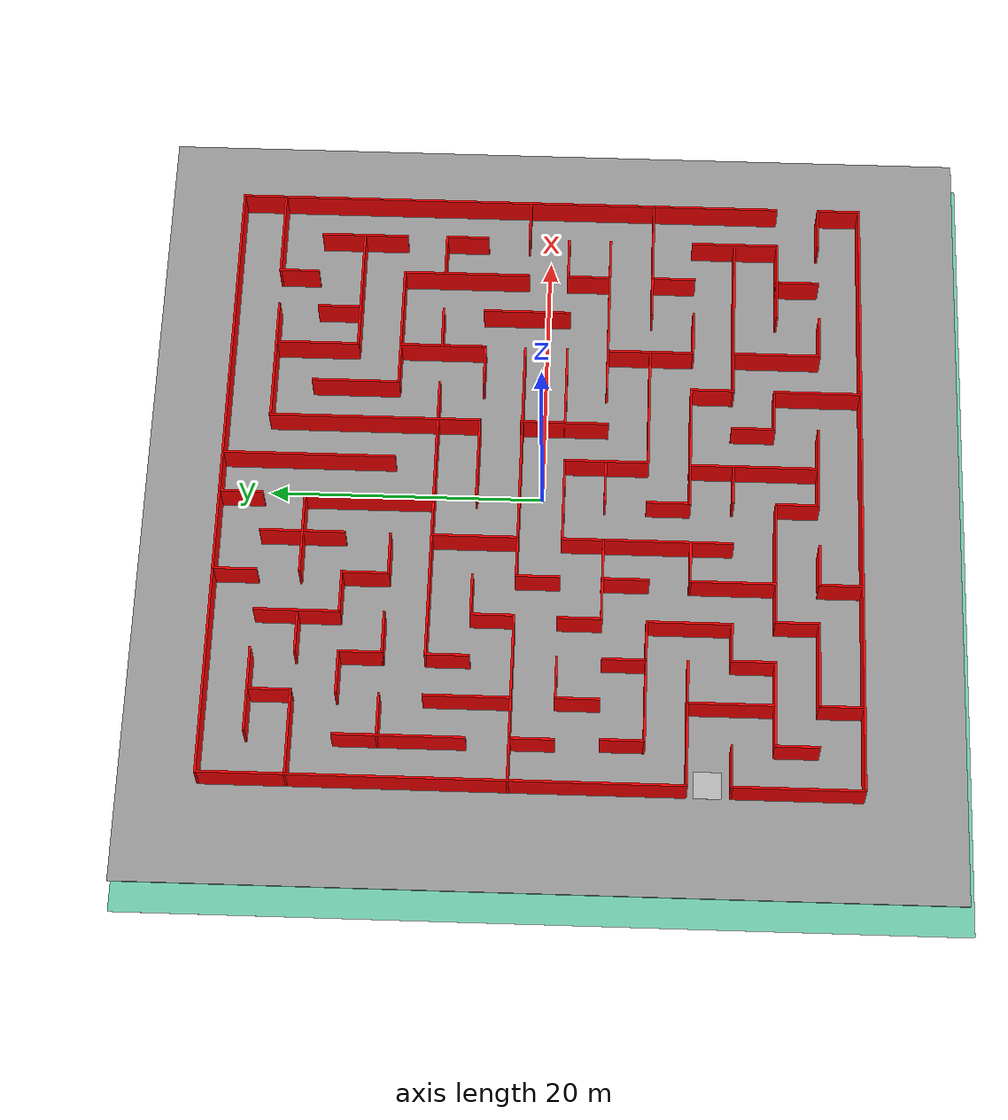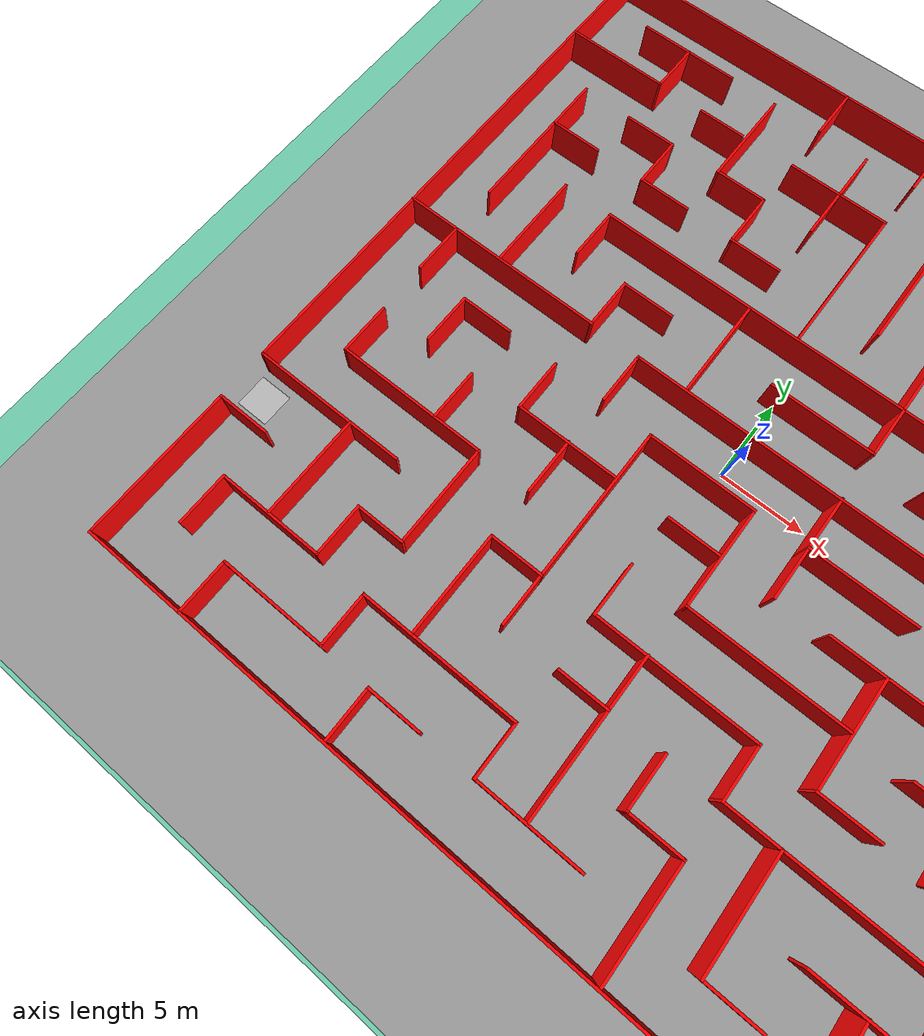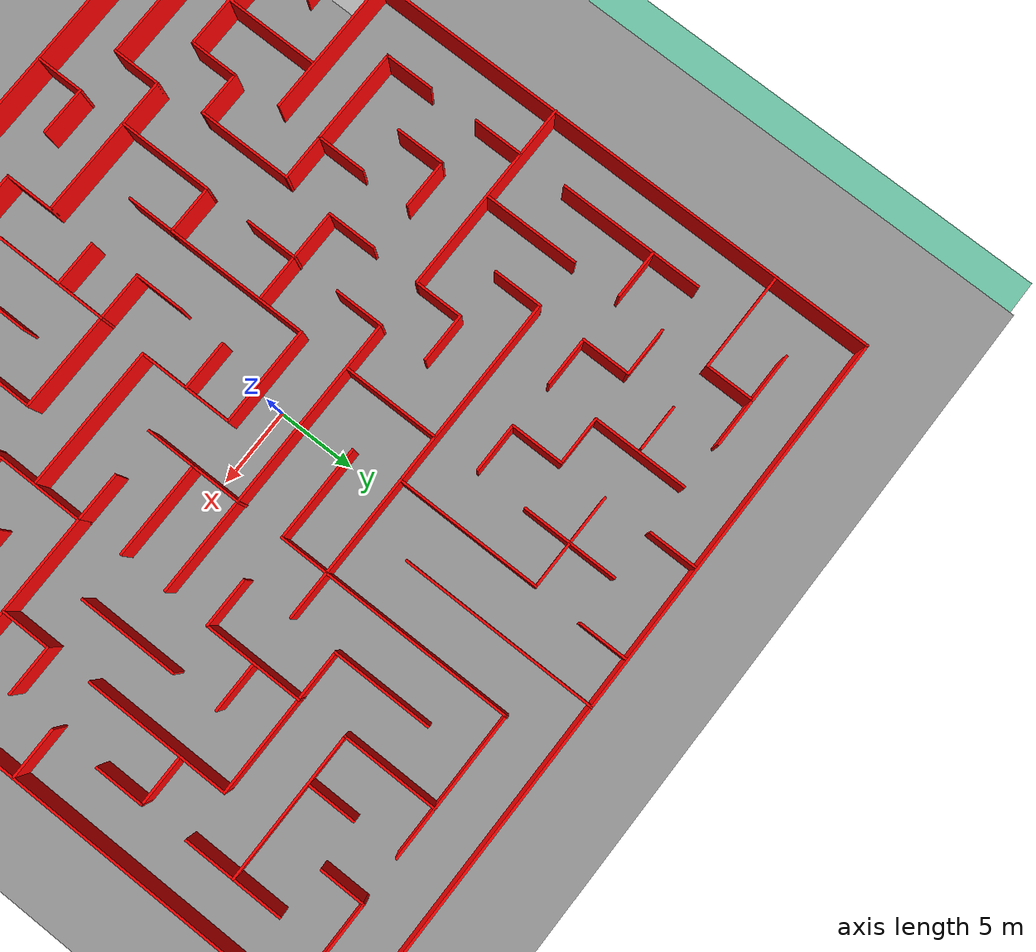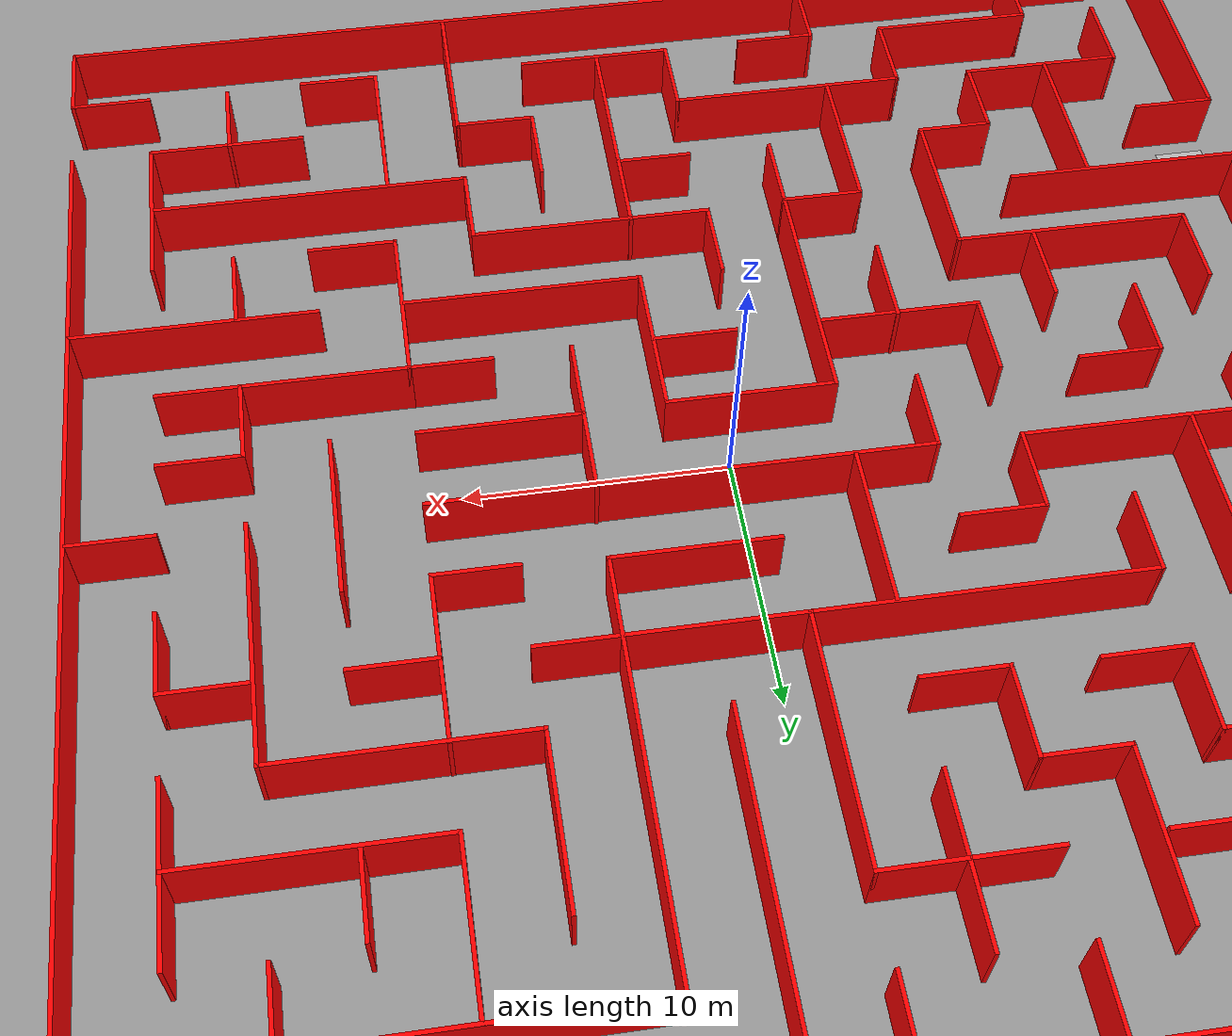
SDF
<sdf version="1.6">
 <world name="default">
  <light name="sun" type="directional">
   <pose>0 0 10 0 -0 0</pose>
   <diffuse>0.8 0.8 0.8 1</diffuse>
   <specular>0.2 0.2 0.2 1</specular>
   <attenuation>
    <range>1000</range>
    <constant>0.9</constant>
    <linear>0.01</linear>
    <quadratic>0.001</quadratic>
   </attenuation>
   <direction>-0.5 0.1 -0.9</direction>
  </light>
  <gravity>0 0 -9.8</gravity>
  <magnetic_field>6e-06 2.3e-05 -4.2e-05</magnetic_field>
  <atmosphere type="adiabatic"/>
  <physics name="default_physics" default="0" type="ode">
   <max_step_size>0.001</max_step_size>
   <real_time_factor>1</real_time_factor>
   <real_time_update_rate>1000</real_time_update_rate>
  </physics>
  <scene><ambient>0.4 0.4 0.4 1</ambient><background>0.7 0.7 0.7 1</background><shadows>1</shadows></scene>
  <audio><device>default</device></audio>
  <spherical_coordinates>
   <surface_model>EARTH_WGS84</surface_model>
   <latitude_deg>0</latitude_deg>
   <longitude_deg>0</longitude_deg>
   <elevation>0</elevation>
   <heading_deg>0</heading_deg>
  </spherical_coordinates>
  <include><uri>model://start_marker</uri><pose>-21.918570 -12.303885 0.026924 0 0 -1.57</pose></include>
  <model name="Final_Maze">
   <pose>-1.35978 -0.782493 0 0 -0 0</pose>
   <link name="Floor_0">
    <collision name="Floor_0_Collision">
     <geometry><box><size>60 60.01 0.1</size></box></geometry>
     <pose>0 0 0.05 0 -0 0</pose>
    </collision>
    <visual name="Floor_0_Visual">
     <pose>0 0 0.05 0 -0 0</pose>
     <geometry><box><size>60 60.01 0.1</size></box></geometry>
     <material>
      <script><uri>file://media/materials/scripts/gazebo.material</uri><name>Gazebo/Grey</name></script>
      <ambient>0 0 0 1</ambient>
     </material>
     <meta><layer>1</layer></meta>
    </visual>
    <pose>1.10022 0.122508 0.001 0 -0 0</pose>
   </link>
   <link name="Wall_0">
    <collision name="Wall_0_Collision">
     <geometry><box><size>60.01 60 0.001</size></box></geometry>
     <pose>0 0 0.0005 0 -0 0</pose>
    </collision>
    <visual name="Wall_0_Visual">
     <pose>0 0 0.0005 0 -0 0</pose>
     <geometry><box><size>60.01 60 0.001</size></box></geometry>
     <material>
      <script><uri>file://media/materials/scripts/gazebo.material</uri><name>Gazebo/Grey</name></script>
      <ambient>0.435294 0.796078 0.67451 1</ambient>
     </material>
     <meta><layer>0</layer></meta>
    </visual>
    <pose>-1.10022 -0.122507 0 0 -0 -1.5708</pose>
   </link>
   <link name="Wall_10">
    <collision name="Wall_10_Collision">
     <geometry><box><size>47 0.15 2.5</size></box></geometry>
     <pose>0 0 1.25 0 -0 0</pose>
    </collision>
    <visual name="Wall_10_Visual">
     <pose>0 0 1.25 0 -0 0</pose>
     <geometry><box><size>47 0.15 2.5</size></box></geometry>
     <material>
      <script><uri>file://media/materials/scripts/gazebo.material</uri><name>Gazebo/Grey</name></script>
      <ambient>1 0 0 1</ambient>
     </material>
     <meta><layer>1</layer></meta>
    </visual>
    <pose>1.9402 -22.4994 0.001 0 -0 0</pose>
   </link>
   <link name="Wall_100">
    <collision name="Wall_100_Collision">
     <geometry><box><size>6.25 0.15 2.5</size></box></geometry>
     <pose>0 0 1.25 0 -0 0</pose>
    </collision>
    <visual name="Wall_100_Visual">
     <pose>0 0 1.25 0 -0 0</pose>
     <geometry><box><size>6.25 0.15 2.5</size></box></geometry>
     <material>
      <script><uri>file://media/materials/scripts/gazebo.material</uri><name>Gazebo/Grey</name></script>
      <ambient>1 0 0 1</ambient>
     </material>
     <meta><layer>1</layer></meta>
    </visual>
    <pose>-15.2625 5.65444 0.001 0 -0 -1.5708</pose>
   </link>
   <link name="Wall_102">
    <collision name="Wall_102_Collision">
     <geometry><box><size>3.25 0.15 2.5</size></box></geometry>
     <pose>0 0 1.25 0 -0 0</pose>
    </collision>
    <visual name="Wall_102_Visual">
     <pose>0 0 1.25 0 -0 0</pose>
     <geometry><box><size>3.25 0.15 2.5</size></box></geometry>
     <material>
      <script><uri>file://media/materials/scripts/gazebo.material</uri><name>Gazebo/Grey</name></script>
      <ambient>1 0 0 1</ambient>
     </material>
     <meta><layer>1</layer></meta>
    </visual>
    <pose>-18.3231 0.892618 0.001 0 -0 -1.5708</pose>
   </link>
   <link name="Wall_104">
    <collision name="Wall_104_Collision">
     <geometry><box><size>3.25 0.15 2.5</size></box></geometry>
     <pose>0 0 1.25 0 -0 0</pose>
    </collision>
    <visual name="Wall_104_Visual">
     <pose>0 0 1.25 0 -0 0</pose>
     <geometry><box><size>3.25 0.15 2.5</size></box></geometry>
     <material>
      <script><uri>file://media/materials/scripts/gazebo.material</uri><name>Gazebo/Grey</name></script>
      <ambient>1 0 0 1</ambient>
     </material>
     <meta><layer>1</layer></meta>
    </visual>
    <pose>-15.1922 -2.19884 0.001 0 -0 1.5708</pose>
   </link>
   <link name="Wall_105">
    <collision name="Wall_105_Collision">
     <geometry><box><size>3.25 0.15 2.5</size></box></geometry>
     <pose>0 0 1.25 0 -0 0</pose>
    </collision>
    <visual name="Wall_105_Visual">
     <pose>0 0 1.25 0 -0 0</pose>
     <geometry><box><size>3.25 0.15 2.5</size></box></geometry>
     <material>
      <script><uri>file://media/materials/scripts/gazebo.material</uri><name>Gazebo/Grey</name></script>
      <ambient>1 0 0 1</ambient>
     </material>
     <meta><layer>1</layer></meta>
    </visual>
    <pose>-13.6422 -0.648844 0.001 0 -0 0</pose>
   </link>
   <link name="Wall_107">
    <collision name="Wall_107_Collision">
     <geometry><box><size>3.25 0.15 2.5</size></box></geometry>
     <pose>0 0 1.25 0 -0 0</pose>
    </collision>
    <visual name="Wall_107_Visual">
     <pose>0 0 1.25 0 -0 0</pose>
     <geometry><box><size>3.25 0.15 2.5</size></box></geometry>
     <material>
      <script><uri>file://media/materials/scripts/gazebo.material</uri><name>Gazebo/Grey</name></script>
      <ambient>1 0 0 1</ambient>
     </material>
     <meta><layer>1</layer></meta>
    </visual>
    <pose>-5.81894 0.918183 0.001 0 -0 1.5708</pose>
   </link>
   <link name="Wall_108">
    <collision name="Wall_108_Collision">
     <geometry><box><size>18.75 0.15 2.5</size></box></geometry>
     <pose>0 0 1.25 0 -0 0</pose>
    </collision>
    <visual name="Wall_108_Visual">
     <pose>0 0 1.25 0 -0 0</pose>
     <geometry><box><size>18.75 0.15 2.5</size></box></geometry>
     <material>
      <script><uri>file://media/materials/scripts/gazebo.material</uri><name>Gazebo/Grey</name></script>
      <ambient>1 0 0 1</ambient>
     </material>
     <meta><layer>1</layer></meta>
    </visual>
    <pose>3.48106 2.46818 0.001 0 -0 0</pose>
   </link>
   <link name="Wall_11">
    <collision name="Wall_11_Collision">
     <geometry><box><size>3.25 0.15 2.5</size></box></geometry>
     <pose>0 0 1.25 0 -0 0</pose>
    </collision>
    <visual name="Wall_11_Visual">
     <pose>0 0 1.25 0 -0 0</pose>
     <geometry><box><size>3.25 0.15 2.5</size></box></geometry>
     <material>
      <script><uri>file://media/materials/scripts/gazebo.material</uri><name>Gazebo/Grey</name></script>
      <ambient>1 0 0 1</ambient>
     </material>
     <meta><layer>1</layer></meta>
    </visual>
    <pose>25.3652 -20.9494 0.001 0 -0 1.5708</pose>
   </link>
   <link name="Wall_110">
    <collision name="Wall_110_Collision">
     <geometry><box><size>6.5 0.15 2.5</size></box></geometry>
     <pose>0 0 1.25 0 -0 0</pose>
    </collision>
    <visual name="Wall_110_Visual">
     <pose>0 0 1.25 0 -0 0</pose>
     <geometry><box><size>6.5 0.15 2.5</size></box></geometry>
     <material>
      <script><uri>file://media/materials/scripts/gazebo.material</uri><name>Gazebo/Grey</name></script>
      <ambient>1 0 0 1</ambient>
     </material>
     <meta><layer>1</layer></meta>
    </visual>
    <pose>6.64947 -0.643191 0.001 0 -0 -1.5708</pose>
   </link>
   <link name="Wall_112">
    <collision name="Wall_112_Collision">
     <geometry><box><size>6.25 0.15 2.5</size></box></geometry>
     <pose>0 0 1.25 0 -0 0</pose>
    </collision>
    <visual name="Wall_112_Visual">
     <pose>0 0 1.25 0 -0 0</pose>
     <geometry><box><size>6.25 0.15 2.5</size></box></geometry>
     <material>
      <script><uri>file://media/materials/scripts/gazebo.material</uri><name>Gazebo/Grey</name></script>
      <ambient>1 0 0 1</ambient>
     </material>
     <meta><layer>1</layer></meta>
    </visual>
    <pose>9.69947 -0.678341 0.001 0 -0 0</pose>
   </link>
   <link name="Wall_114">
    <collision name="Wall_114_Collision">
     <geometry><box><size>6.5 0.15 2.5</size></box></geometry>
     <pose>0 0 1.25 0 -0 0</pose>
    </collision>
    <visual name="Wall_114_Visual">
     <pose>0 0 1.25 0 -0 0</pose>
     <geometry><box><size>6.5 0.15 2.5</size></box></geometry>
     <material>
      <script><uri>file://media/materials/scripts/gazebo.material</uri><name>Gazebo/Grey</name></script>
      <ambient>1 0 0 1</ambient>
     </material>
     <meta><layer>1</layer></meta>
    </visual>
    <pose>15.9026 2.43389 0.001 0 -0 -1.5708</pose>
   </link>
   <link name="Wall_116">
    <collision name="Wall_116_Collision">
     <geometry><box><size>6.25 0.15 2.5</size></box></geometry>
     <pose>0 0 1.25 0 -0 0</pose>
    </collision>
    <visual name="Wall_116_Visual">
     <pose>0 0 1.25 0 -0 0</pose>
     <geometry><box><size>6.25 0.15 2.5</size></box></geometry>
     <material>
      <script><uri>file://media/materials/scripts/gazebo.material</uri><name>Gazebo/Grey</name></script>
      <ambient>1 0 0 1</ambient>
     </material>
     <meta><layer>1</layer></meta>
    </visual>
    <pose>3.63212 5.60889 0.001 0 -0 0</pose>
   </link>
   <link name="Wall_117">
    <collision name="Wall_117_Collision">
     <geometry><box><size>15.6407 0.15 2.5</size></box></geometry>
     <pose>0 0 1.25 0 -0 0</pose>
    </collision>
    <visual name="Wall_117_Visual">
     <pose>0 0 1.25 0 -0 0</pose>
     <geometry><box><size>15.6407 0.15 2.5</size></box></geometry>
     <material>
      <script><uri>file://media/materials/scripts/gazebo.material</uri><name>Gazebo/Grey</name></script>
      <ambient>1 0 0 1</ambient>
     </material>
     <meta><layer>1</layer></meta>
    </visual>
    <pose>6.68212 13.3542 0.001 0 -0 1.5708</pose>
   </link>
   <link name="Wall_118">
    <collision name="Wall_118_Collision">
     <geometry><box><size>9.5 0.15 2.5</size></box></geometry>
     <pose>0 0 1.25 0 -0 0</pose>
    </collision>
    <visual name="Wall_118_Visual">
     <pose>0 0 1.25 0 -0 0</pose>
     <geometry><box><size>9.5 0.15 2.5</size></box></geometry>
     <material>
      <script><uri>file://media/materials/scripts/gazebo.material</uri><name>Gazebo/Grey</name></script>
      <ambient>1 0 0 1</ambient>
     </material>
     <meta><layer>1</layer></meta>
    </visual>
    <pose>11.3571 21.0644 0.001 0 -0 0</pose>
   </link>
   <link name="Wall_12">
    <collision name="Wall_12_Collision">
     <geometry><box><size>3.25 0.15 2.5</size></box></geometry>
     <pose>0 0 1.25 0 -0 0</pose>
    </collision>
    <visual name="Wall_12_Visual">
     <pose>0 0 1.25 0 -0 0</pose>
     <geometry><box><size>3.25 0.15 2.5</size></box></geometry>
     <material>
      <script><uri>file://media/materials/scripts/gazebo.material</uri><name>Gazebo/Grey</name></script>
      <ambient>1 0 0 1</ambient>
     </material>
     <meta><layer>1</layer></meta>
    </visual>
    <pose>23.8152 -19.3994 0.001 0 -0 3.14159</pose>
   </link>
   <link name="Wall_120">
    <collision name="Wall_120_Collision">
     <geometry><box><size>3 0.15 2.5</size></box></geometry>
     <pose>0 0 1.25 0 -0 0</pose>
    </collision>
    <visual name="Wall_120_Visual">
     <pose>0 0 1.25 0 -0 0</pose>
     <geometry><box><size>3 0.15 2.5</size></box></geometry>
     <material>
      <script><uri>file://media/materials/scripts/gazebo.material</uri><name>Gazebo/Grey</name></script>
      <ambient>1 0 0 1</ambient>
     </material>
     <meta><layer>1</layer></meta>
    </visual>
    <pose>18.9322 19.7481 0.001 0 -0 1.5708</pose>
   </link>
   <link name="Wall_123">
    <collision name="Wall_123_Collision">
     <geometry><box><size>6.5 0.15 2.5</size></box></geometry>
     <pose>0 0 1.25 0 -0 0</pose>
    </collision>
    <visual name="Wall_123_Visual">
     <pose>0 0 1.25 0 -0 0</pose>
     <geometry><box><size>6.5 0.15 2.5</size></box></geometry>
     <material>
      <script><uri>file://media/materials/scripts/gazebo.material</uri><name>Gazebo/Grey</name></script>
      <ambient>1 0 0 1</ambient>
     </material>
     <meta><layer>1</layer></meta>
    </visual>
    <pose>22.1067 21.1714 0.001 0 -0 3.14159</pose>
   </link>
   <link name="Wall_125">
    <collision name="Wall_125_Collision">
     <geometry><box><size>6.25 0.15 2.5</size></box></geometry>
     <pose>0 0 1.25 0 -0 0</pose>
    </collision>
    <visual name="Wall_125_Visual">
     <pose>0 0 1.25 0 -0 0</pose>
     <geometry><box><size>6.25 0.15 2.5</size></box></geometry>
     <material>
      <script><uri>file://media/materials/scripts/gazebo.material</uri><name>Gazebo/Grey</name></script>
      <ambient>1 0 0 1</ambient>
     </material>
     <meta><layer>1</layer></meta>
    </visual>
    <pose>12.7989 18.0067 0.001 0 -0 -1.5708</pose>
   </link>
   <link name="Wall_126">
    <collision name="Wall_126_Collision">
     <geometry><box><size>9.5 0.15 2.5</size></box></geometry>
     <pose>0 0 1.25 0 -0 0</pose>
    </collision>
    <visual name="Wall_126_Visual">
     <pose>0 0 1.25 0 -0 0</pose>
     <geometry><box><size>9.5 0.15 2.5</size></box></geometry>
     <material>
      <script><uri>file://media/materials/scripts/gazebo.material</uri><name>Gazebo/Grey</name></script>
      <ambient>1 0 0 1</ambient>
     </material>
     <meta><layer>1</layer></meta>
    </visual>
    <pose>17.4739 14.9567 0.001 0 -0 0</pose>
   </link>
   <link name="Wall_128">
    <collision name="Wall_128_Collision">
     <geometry><box><size>3.25 0.15 2.5</size></box></geometry>
     <pose>0 0 1.25 0 -0 0</pose>
    </collision>
    <visual name="Wall_128_Visual">
     <pose>0 0 1.25 0 -0 0</pose>
     <geometry><box><size>3.25 0.15 2.5</size></box></geometry>
     <material>
      <script><uri>file://media/materials/scripts/gazebo.material</uri><name>Gazebo/Grey</name></script>
      <ambient>1 0 0 1</ambient>
     </material>
     <meta><layer>1</layer></meta>
    </visual>
    <pose>15.9497 16.5394 0.001 0 -0 -1.5708</pose>
   </link>
   <link name="Wall_130">
    <collision name="Wall_130_Collision">
     <geometry><box><size>6.5 0.15 2.5</size></box></geometry>
     <pose>0 0 1.25 0 -0 0</pose>
    </collision>
    <visual name="Wall_130_Visual">
     <pose>0 0 1.25 0 -0 0</pose>
     <geometry><box><size>6.5 0.15 2.5</size></box></geometry>
     <material>
      <script><uri>file://media/materials/scripts/gazebo.material</uri><name>Gazebo/Grey</name></script>
      <ambient>1 0 0 1</ambient>
     </material>
     <meta><layer>1</layer></meta>
    </visual>
    <pose>22.1595 14.945 0.001 0 -0 -1.5708</pose>
   </link>
   <link name="Wall_132">
    <collision name="Wall_132_Collision">
     <geometry><box><size>6.5 0.15 2.5</size></box></geometry>
     <pose>0 0 1.25 0 -0 0</pose>
    </collision>
    <visual name="Wall_132_Visual">
     <pose>0 0 1.25 0 -0 0</pose>
     <geometry><box><size>6.5 0.15 2.5</size></box></geometry>
     <material>
      <script><uri>file://media/materials/scripts/gazebo.material</uri><name>Gazebo/Grey</name></script>
      <ambient>1 0 0 1</ambient>
     </material>
     <meta><layer>1</layer></meta>
    </visual>
    <pose>9.67868 14.945 0.001 0 -0 -1.5708</pose>
   </link>
   <link name="Wall_133">
    <collision name="Wall_133_Collision">
     <geometry><box><size>9.5 0.15 2.5</size></box></geometry>
     <pose>0 0 1.25 0 -0 0</pose>
    </collision>
    <visual name="Wall_133_Visual">
     <pose>0 0 1.25 0 -0 0</pose>
     <geometry><box><size>9.5 0.15 2.5</size></box></geometry>
     <material>
      <script><uri>file://media/materials/scripts/gazebo.material</uri><name>Gazebo/Grey</name></script>
      <ambient>1 0 0 1</ambient>
     </material>
     <meta><layer>1</layer></meta>
    </visual>
    <pose>14.3537 11.77 0.001 0 -0 0</pose>
   </link>
   <link name="Wall_134">
    <collision name="Wall_134_Collision">
     <geometry><box><size>9.5 0.15 2.5</size></box></geometry>
     <pose>0 0 1.25 0 -0 0</pose>
    </collision>
    <visual name="Wall_134_Visual">
     <pose>0 0 1.25 0 -0 0</pose>
     <geometry><box><size>9.5 0.15 2.5</size></box></geometry>
     <material>
      <script><uri>file://media/materials/scripts/gazebo.material</uri><name>Gazebo/Grey</name></script>
      <ambient>1 0 0 1</ambient>
     </material>
     <meta><layer>1</layer></meta>
    </visual>
    <pose>19.0287 7.09502 0.001 0 -0 -1.5708</pose>
   </link>
   <link name="Wall_136">
    <collision name="Wall_136_Collision">
     <geometry><box><size>9.5 0.15 2.5</size></box></geometry>
     <pose>0 0 1.25 0 -0 0</pose>
    </collision>
    <visual name="Wall_136_Visual">
     <pose>0 0 1.25 0 -0 0</pose>
     <geometry><box><size>9.5 0.15 2.5</size></box></geometry>
     <material>
      <script><uri>file://media/materials/scripts/gazebo.material</uri><name>Gazebo/Grey</name></script>
      <ambient>1 0 0 1</ambient>
     </material>
     <meta><layer>1</layer></meta>
    </visual>
    <pose>-18.3879 10.295 0.001 0 -0 -1.5708</pose>
   </link>
   <link name="Wall_138">
    <collision name="Wall_138_Collision">
     <geometry><box><size>3.25 0.15 2.5</size></box></geometry>
     <pose>0 0 1.25 0 -0 0</pose>
    </collision>
    <visual name="Wall_138_Visual">
     <pose>0 0 1.25 0 -0 0</pose>
     <geometry><box><size>3.25 0.15 2.5</size></box></geometry>
     <material>
      <script><uri>file://media/materials/scripts/gazebo.material</uri><name>Gazebo/Grey</name></script>
      <ambient>1 0 0 1</ambient>
     </material>
     <meta><layer>1</layer></meta>
    </visual>
    <pose>-16.8379 11.8391 0.001 0 -0 0</pose>
   </link>
   <link name="Wall_14">
    <collision name="Wall_14_Collision">
     <geometry><box><size>3.25 0.15 2.5</size></box></geometry>
     <pose>0 0 1.25 0 -0 0</pose>
    </collision>
    <visual name="Wall_14_Visual">
     <pose>0 0 1.25 0 -0 0</pose>
     <geometry><box><size>3.25 0.15 2.5</size></box></geometry>
     <material>
      <script><uri>file://media/materials/scripts/gazebo.material</uri><name>Gazebo/Grey</name></script>
      <ambient>1 0 0 1</ambient>
     </material>
     <meta><layer>1</layer></meta>
    </visual>
    <pose>-15.2471 -20.8919 0.001 0 -0 1.5708</pose>
   </link>
   <link name="Wall_140">
    <collision name="Wall_140_Collision">
     <geometry><box><size>3.25 0.15 2.5</size></box></geometry>
     <pose>0 0 1.25 0 -0 0</pose>
    </collision>
    <visual name="Wall_140_Visual">
     <pose>0 0 1.25 0 -0 0</pose>
     <geometry><box><size>3.25 0.15 2.5</size></box></geometry>
     <material>
      <script><uri>file://media/materials/scripts/gazebo.material</uri><name>Gazebo/Grey</name></script>
      <ambient>1 0 0 1</ambient>
     </material>
     <meta><layer>1</layer></meta>
    </visual>
    <pose>-13.6366 14.8996 0.001 0 -0 0</pose>
   </link>
   <link name="Wall_141">
    <collision name="Wall_141_Collision">
     <geometry><box><size>3.25 0.15 2.5</size></box></geometry>
     <pose>0 0 1.25 0 -0 0</pose>
    </collision>
    <visual name="Wall_141_Visual">
     <pose>0 0 1.25 0 -0 0</pose>
     <geometry><box><size>3.25 0.15 2.5</size></box></geometry>
     <material>
      <script><uri>file://media/materials/scripts/gazebo.material</uri><name>Gazebo/Grey</name></script>
      <ambient>1 0 0 1</ambient>
     </material>
     <meta><layer>1</layer></meta>
    </visual>
    <pose>-12.0867 13.3496 0.001 0 -0 -1.5708</pose>
   </link>
   <link name="Wall_142">
    <collision name="Wall_142_Collision">
     <geometry><box><size>3.25 0.15 2.5</size></box></geometry>
     <pose>0 0 1.25 0 -0 0</pose>
    </collision>
    <visual name="Wall_142_Visual">
     <pose>0 0 1.25 0 -0 0</pose>
     <geometry><box><size>3.25 0.15 2.5</size></box></geometry>
     <material>
      <script><uri>file://media/materials/scripts/gazebo.material</uri><name>Gazebo/Grey</name></script>
      <ambient>1 0 0 1</ambient>
     </material>
     <meta><layer>1</layer></meta>
    </visual>
    <pose>-10.5367 11.7996 0.001 0 -0 0</pose>
   </link>
   <link name="Wall_144">
    <collision name="Wall_144_Collision">
     <geometry><box><size>22 0.15 2.5</size></box></geometry>
     <pose>0 0 1.25 0 -0 0</pose>
    </collision>
    <visual name="Wall_144_Visual">
     <pose>0 0 1.25 0 -0 0</pose>
     <geometry><box><size>22 0.15 2.5</size></box></geometry>
     <material>
      <script><uri>file://media/materials/scripts/gazebo.material</uri><name>Gazebo/Grey</name></script>
      <ambient>1 0 0 1</ambient>
     </material>
     <meta><layer>1</layer></meta>
    </visual>
    <pose>-1.2011 8.70815 0.001 0 -0 0</pose>
   </link>
   <link name="Wall_146">
    <collision name="Wall_146_Collision">
     <geometry><box><size>3.25 0.15 2.5</size></box></geometry>
     <pose>0 0 1.25 0 -0 0</pose>
    </collision>
    <visual name="Wall_146_Visual">
     <pose>0 0 1.25 0 -0 0</pose>
     <geometry><box><size>3.25 0.15 2.5</size></box></geometry>
     <material>
      <script><uri>file://media/materials/scripts/gazebo.material</uri><name>Gazebo/Grey</name></script>
      <ambient>1 0 0 1</ambient>
     </material>
     <meta><layer>1</layer></meta>
    </visual>
    <pose>-12.1261 7.15815 0.001 0 -0 -1.5708</pose>
   </link>
   <link name="Wall_148">
    <collision name="Wall_148_Collision">
     <geometry><box><size>6.25 0.15 2.5</size></box></geometry>
     <pose>0 0 1.25 0 -0 0</pose>
    </collision>
    <visual name="Wall_148_Visual">
     <pose>0 0 1.25 0 -0 0</pose>
     <geometry><box><size>6.25 0.15 2.5</size></box></geometry>
     <material>
      <script><uri>file://media/materials/scripts/gazebo.material</uri><name>Gazebo/Grey</name></script>
      <ambient>1 0 0 1</ambient>
     </material>
     <meta><layer>1</layer></meta>
    </visual>
    <pose>-2.76855 5.58779 0.001 0 -0 -1.5708</pose>
   </link>
   <link name="Wall_15">
    <collision name="Wall_15_Collision">
     <geometry><box><size>6.5 0.15 2.5</size></box></geometry>
     <pose>0 0 1.25 0 -0 0</pose>
    </collision>
    <visual name="Wall_15_Visual">
     <pose>0 0 1.25 0 -0 0</pose>
     <geometry><box><size>6.5 0.15 2.5</size></box></geometry>
     <material>
      <script><uri>file://media/materials/scripts/gazebo.material</uri><name>Gazebo/Grey</name></script>
      <ambient>1 0 0 1</ambient>
     </material>
     <meta><layer>1</layer></meta>
    </visual>
    <pose>-12.0721 -19.3419 0.001 0 -0 0</pose>
   </link>
   <link name="Wall_153">
    <collision name="Wall_153_Collision">
     <geometry><box><size>6.5 0.15 2.5</size></box></geometry>
     <pose>0 0 1.25 0 -0 0</pose>
    </collision>
    <visual name="Wall_153_Visual">
     <pose>0 0 1.25 0 -0 0</pose>
     <geometry><box><size>6.5 0.15 2.5</size></box></geometry>
     <material>
      <script><uri>file://media/materials/scripts/gazebo.material</uri><name>Gazebo/Grey</name></script>
      <ambient>1 0 0 1</ambient>
     </material>
     <meta><layer>1</layer></meta>
    </visual>
    <pose>12.8337 8.61794 0.001 0 -0 -1.5708</pose>
   </link>
   <link name="Wall_154">
    <collision name="Wall_154_Collision">
     <geometry><box><size>3.25 0.15 2.5</size></box></geometry>
     <pose>0 0 1.25 0 -0 0</pose>
    </collision>
    <visual name="Wall_154_Visual">
     <pose>0 0 1.25 0 -0 0</pose>
     <geometry><box><size>3.25 0.15 2.5</size></box></geometry>
     <material>
      <script><uri>file://media/materials/scripts/gazebo.material</uri><name>Gazebo/Grey</name></script>
      <ambient>1 0 0 1</ambient>
     </material>
     <meta><layer>1</layer></meta>
    </visual>
    <pose>11.2837 5.44294 0.001 0 -0 3.14159</pose>
   </link>
   <link name="Wall_156">
    <collision name="Wall_156_Collision">
     <geometry><box><size>3.25 0.15 2.5</size></box></geometry>
     <pose>0 0 1.25 0 -0 0</pose>
    </collision>
    <visual name="Wall_156_Visual">
     <pose>0 0 1.25 0 -0 0</pose>
     <geometry><box><size>3.25 0.15 2.5</size></box></geometry>
     <material>
      <script><uri>file://media/materials/scripts/gazebo.material</uri><name>Gazebo/Grey</name></script>
      <ambient>1 0 0 1</ambient>
     </material>
     <meta><layer>1</layer></meta>
    </visual>
    <pose>14.4239 8.69545 0.001 0 -0 0</pose>
   </link>
   <link name="Wall_158">
    <collision name="Wall_158_Collision">
     <geometry><box><size>6.5 0.15 2.5</size></box></geometry>
     <pose>0 0 1.25 0 -0 0</pose>
    </collision>
    <visual name="Wall_158_Visual">
     <pose>0 0 1.25 0 -0 0</pose>
     <geometry><box><size>6.5 0.15 2.5</size></box></geometry>
     <material>
      <script><uri>file://media/materials/scripts/gazebo.material</uri><name>Gazebo/Grey</name></script>
      <ambient>1 0 0 1</ambient>
     </material>
     <meta><layer>1</layer></meta>
    </visual>
    <pose>-18.3166 18.0907 0.001 0 -0 0</pose>
   </link>
   <link name="Wall_159">
    <collision name="Wall_159_Collision">
     <geometry><box><size>3.25 0.15 2.5</size></box></geometry>
     <pose>0 0 1.25 0 -0 0</pose>
    </collision>
    <visual name="Wall_159_Visual">
     <pose>0 0 1.25 0 -0 0</pose>
     <geometry><box><size>3.25 0.15 2.5</size></box></geometry>
     <material>
      <script><uri>file://media/materials/scripts/gazebo.material</uri><name>Gazebo/Grey</name></script>
      <ambient>1 0 0 1</ambient>
     </material>
     <meta><layer>1</layer></meta>
    </visual>
    <pose>-15.1416 19.6407 0.001 0 -0 1.5708</pose>
   </link>
   <link name="Wall_16">
    <collision name="Wall_16_Collision">
     <geometry><box><size>3.25 0.15 2.5</size></box></geometry>
     <pose>0 0 1.25 0 -0 0</pose>
    </collision>
    <visual name="Wall_16_Visual">
     <pose>0 0 1.25 0 -0 0</pose>
     <geometry><box><size>3.25 0.15 2.5</size></box></geometry>
     <material>
      <script><uri>file://media/materials/scripts/gazebo.material</uri><name>Gazebo/Grey</name></script>
      <ambient>1 0 0 1</ambient>
     </material>
     <meta><layer>1</layer></meta>
    </visual>
    <pose>-8.89709 -17.7919 0.001 0 -0 1.5708</pose>
   </link>
   <link name="Wall_160">
    <collision name="Wall_160_Collision">
     <geometry><box><size>3.25 0.15 2.5</size></box></geometry>
     <pose>0 0 1.25 0 -0 0</pose>
    </collision>
    <visual name="Wall_160_Visual">
     <pose>0 0 1.25 0 -0 0</pose>
     <geometry><box><size>3.25 0.15 2.5</size></box></geometry>
     <material>
      <script><uri>file://media/materials/scripts/gazebo.material</uri><name>Gazebo/Grey</name></script>
      <ambient>1 0 0 1</ambient>
     </material>
     <meta><layer>1</layer></meta>
    </visual>
    <pose>-16.6916 21.1907 0.001 0 -0 3.14159</pose>
   </link>
   <link name="Wall_162">
    <collision name="Wall_162_Collision">
     <geometry><box><size>3.25 0.15 2.5</size></box></geometry>
     <pose>0 0 1.25 0 -0 0</pose>
    </collision>
    <visual name="Wall_162_Visual">
     <pose>0 0 1.25 0 -0 0</pose>
     <geometry><box><size>3.25 0.15 2.5</size></box></geometry>
     <material>
      <script><uri>file://media/materials/scripts/gazebo.material</uri><name>Gazebo/Grey</name></script>
      <ambient>1 0 0 1</ambient>
     </material>
     <meta><layer>1</layer></meta>
    </visual>
    <pose>-13.5916 21.1907 0.001 0 -0 0</pose>
   </link>
   <link name="Wall_164">
    <collision name="Wall_164_Collision">
     <geometry><box><size>3 0.15 2.5</size></box></geometry>
     <pose>0 0 1.25 0 -0 0</pose>
    </collision>
    <visual name="Wall_164_Visual">
     <pose>0 0 1.25 0 -0 0</pose>
     <geometry><box><size>3 0.15 2.5</size></box></geometry>
     <material>
      <script><uri>file://media/materials/scripts/gazebo.material</uri><name>Gazebo/Grey</name></script>
      <ambient>1 0 0 1</ambient>
     </material>
     <meta><layer>1</layer></meta>
    </visual>
    <pose>-10.6862 18.0147 0.001 0 -0 0</pose>
   </link>
   <link name="Wall_166">
    <collision name="Wall_166_Collision">
     <geometry><box><size>6.25 0.15 2.5</size></box></geometry>
     <pose>0 0 1.25 0 -0 0</pose>
    </collision>
    <visual name="Wall_166_Visual">
     <pose>0 0 1.25 0 -0 0</pose>
     <geometry><box><size>6.25 0.15 2.5</size></box></geometry>
     <material>
      <script><uri>file://media/materials/scripts/gazebo.material</uri><name>Gazebo/Grey</name></script>
      <ambient>1 0 0 1</ambient>
     </material>
     <meta><layer>1</layer></meta>
    </visual>
    <pose>-8.99797 18.078 0.001 0 -0 -1.5708</pose>
   </link>
   <link name="Wall_169">
    <collision name="Wall_169_Collision">
     <geometry><box><size>3.25 0.15 2.5</size></box></geometry>
     <pose>0 0 1.25 0 -0 0</pose>
    </collision>
    <visual name="Wall_169_Visual">
     <pose>0 0 1.25 0 -0 0</pose>
     <geometry><box><size>3.25 0.15 2.5</size></box></geometry>
     <material>
      <script><uri>file://media/materials/scripts/gazebo.material</uri><name>Gazebo/Grey</name></script>
      <ambient>1 0 0 1</ambient>
     </material>
     <meta><layer>1</layer></meta>
    </visual>
    <pose>-7.44797 15.028 0.001 0 -0 0</pose>
   </link>
   <link name="Wall_17">
    <collision name="Wall_17_Collision">
     <geometry><box><size>9.5 0.15 2.5</size></box></geometry>
     <pose>0 0 1.25 0 -0 0</pose>
    </collision>
    <visual name="Wall_17_Visual">
     <pose>0 0 1.25 0 -0 0</pose>
     <geometry><box><size>9.5 0.15 2.5</size></box></geometry>
     <material>
      <script><uri>file://media/materials/scripts/gazebo.material</uri><name>Gazebo/Grey</name></script>
      <ambient>1 0 0 1</ambient>
     </material>
     <meta><layer>1</layer></meta>
    </visual>
    <pose>-4.22209 -16.2419 0.001 0 -0 0</pose>
   </link>
   <link name="Wall_170">
    <collision name="Wall_170_Collision">
     <geometry><box><size>3.5 0.15 2.5</size></box></geometry>
     <pose>0 0 1.25 0 -0 0</pose>
    </collision>
    <visual name="Wall_170_Visual">
     <pose>0 0 1.25 0 -0 0</pose>
     <geometry><box><size>3.5 0.15 2.5</size></box></geometry>
     <material>
      <script><uri>file://media/materials/scripts/gazebo.material</uri><name>Gazebo/Grey</name></script>
      <ambient>1 0 0 1</ambient>
     </material>
     <meta><layer>1</layer></meta>
    </visual>
    <pose>-5.89797 13.353 0.001 0 -0 -1.5708</pose>
   </link>
   <link name="Wall_171">
    <collision name="Wall_171_Collision">
     <geometry><box><size>3.25 0.15 2.5</size></box></geometry>
     <pose>0 0 1.25 0 -0 0</pose>
    </collision>
    <visual name="Wall_171_Visual">
     <pose>0 0 1.25 0 -0 0</pose>
     <geometry><box><size>3.25 0.15 2.5</size></box></geometry>
     <material>
      <script><uri>file://media/materials/scripts/gazebo.material</uri><name>Gazebo/Grey</name></script>
      <ambient>1 0 0 1</ambient>
     </material>
     <meta><layer>1</layer></meta>
    </visual>
    <pose>-4.34797 11.678 0.001 0 -0 0</pose>
   </link>
   <link name="Wall_173">
    <collision name="Wall_173_Collision">
     <geometry><box><size>3.25 0.15 2.5</size></box></geometry>
     <pose>0 0 1.25 0 -0 0</pose>
    </collision>
    <visual name="Wall_173_Visual">
     <pose>0 0 1.25 0 -0 0</pose>
     <geometry><box><size>3.25 0.15 2.5</size></box></geometry>
     <material>
      <script><uri>file://media/materials/scripts/gazebo.material</uri><name>Gazebo/Grey</name></script>
      <ambient>1 0 0 1</ambient>
     </material>
     <meta><layer>1</layer></meta>
    </visual>
    <pose>-5.88474 22.7612 0.001 0 -0 -1.5708</pose>
   </link>
   <link name="Wall_175">
    <collision name="Wall_175_Collision">
     <geometry><box><size>6.25 0.15 2.5</size></box></geometry>
     <pose>0 0 1.25 0 -0 0</pose>
    </collision>
    <visual name="Wall_175_Visual">
     <pose>0 0 1.25 0 -0 0</pose>
     <geometry><box><size>6.25 0.15 2.5</size></box></geometry>
     <material>
      <script><uri>file://media/materials/scripts/gazebo.material</uri><name>Gazebo/Grey</name></script>
      <ambient>1 0 0 1</ambient>
     </material>
     <meta><layer>1</layer></meta>
    </visual>
    <pose>-2.79976 18.0847 0.001 0 -0 0</pose>
   </link>
   <link name="Wall_176">
    <collision name="Wall_176_Collision">
     <geometry><box><size>9.5 0.15 2.5</size></box></geometry>
     <pose>0 0 1.25 0 -0 0</pose>
    </collision>
    <visual name="Wall_176_Visual">
     <pose>0 0 1.25 0 -0 0</pose>
     <geometry><box><size>9.5 0.15 2.5</size></box></geometry>
     <material>
      <script><uri>file://media/materials/scripts/gazebo.material</uri><name>Gazebo/Grey</name></script>
      <ambient>1 0 0 1</ambient>
     </material>
     <meta><layer>1</layer></meta>
    </visual>
    <pose>0.250245 13.4097 0.001 0 -0 -1.5708</pose>
   </link>
   <link name="Wall_178">
    <collision name="Wall_178_Collision">
     <geometry><box><size>6.25 0.15 2.5</size></box></geometry>
     <pose>0 0 1.25 0 -0 0</pose>
    </collision>
    <visual name="Wall_178_Visual">
     <pose>0 0 1.25 0 -0 0</pose>
     <geometry><box><size>6.25 0.15 2.5</size></box></geometry>
     <material>
      <script><uri>file://media/materials/scripts/gazebo.material</uri><name>Gazebo/Grey</name></script>
      <ambient>1 0 0 1</ambient>
     </material>
     <meta><layer>1</layer></meta>
    </visual>
    <pose>-2.73652 18.078 0.001 0 -0 -1.5708</pose>
   </link>
   <link name="Wall_18">
    <collision name="Wall_18_Collision">
     <geometry><box><size>3.25 0.15 2.5</size></box></geometry>
     <pose>0 0 1.25 0 -0 0</pose>
    </collision>
    <visual name="Wall_18_Visual">
     <pose>0 0 1.25 0 -0 0</pose>
     <geometry><box><size>3.25 0.15 2.5</size></box></geometry>
     <material>
      <script><uri>file://media/materials/scripts/gazebo.material</uri><name>Gazebo/Grey</name></script>
      <ambient>1 0 0 1</ambient>
     </material>
     <meta><layer>1</layer></meta>
    </visual>
    <pose>0.452914 -17.7919 0.001 0 -0 -1.5708</pose>
   </link>
   <link name="Wall_182">
    <collision name="Wall_182_Collision">
     <geometry><box><size>3.25 0.15 2.5</size></box></geometry>
     <pose>0 0 1.25 0 -0 0</pose>
    </collision>
    <visual name="Wall_182_Visual">
     <pose>0 0 1.25 0 -0 0</pose>
     <geometry><box><size>3.25 0.15 2.5</size></box></geometry>
     <material>
      <script><uri>file://media/materials/scripts/gazebo.material</uri><name>Gazebo/Grey</name></script>
      <ambient>1 0 0 1</ambient>
     </material>
     <meta><layer>1</layer></meta>
    </visual>
    <pose>0.333185 22.7748 0.001 0 -0 -1.5708</pose>
   </link>
   <link name="Wall_184">
    <collision name="Wall_184_Collision">
     <geometry><box><size>12.75 0.15 2.5</size></box></geometry>
     <pose>0 0 1.25 0 -0 0</pose>
    </collision>
    <visual name="Wall_184_Visual">
     <pose>0 0 1.25 0 -0 0</pose>
     <geometry><box><size>12.75 0.15 2.5</size></box></geometry>
     <material>
      <script><uri>file://media/materials/scripts/gazebo.material</uri><name>Gazebo/Grey</name></script>
      <ambient>1 0 0 1</ambient>
     </material>
     <meta><layer>1</layer></meta>
    </visual>
    <pose>3.48419 18.0248 0.001 0 -0 -1.5708</pose>
   </link>
   <link name="Wall_186">
    <collision name="Wall_186_Collision">
     <geometry><box><size>3.25 0.15 2.5</size></box></geometry>
     <pose>0 0 1.25 0 -0 0</pose>
    </collision>
    <visual name="Wall_186_Visual">
     <pose>0 0 1.25 0 -0 0</pose>
     <geometry><box><size>3.25 0.15 2.5</size></box></geometry>
     <material>
      <script><uri>file://media/materials/scripts/gazebo.material</uri><name>Gazebo/Grey</name></script>
      <ambient>1 0 0 1</ambient>
     </material>
     <meta><layer>1</layer></meta>
    </visual>
    <pose>20.6558 8.72552 0.001 0 -0 0</pose>
   </link>
   <link name="Wall_187">
    <collision name="Wall_187_Collision">
     <geometry><box><size>3.25 0.15 2.5</size></box></geometry>
     <pose>0 0 1.25 0 -0 0</pose>
    </collision>
    <visual name="Wall_187_Visual">
     <pose>0 0 1.25 0 -0 0</pose>
     <geometry><box><size>3.25 0.15 2.5</size></box></geometry>
     <material>
      <script><uri>file://media/materials/scripts/gazebo.material</uri><name>Gazebo/Grey</name></script>
      <ambient>1 0 0 1</ambient>
     </material>
     <meta><layer>1</layer></meta>
    </visual>
    <pose>22.2058 7.17552 0.001 0 -0 -1.5708</pose>
   </link>
   <link name="Wall_189">
    <collision name="Wall_189_Collision">
     <geometry><box><size>3.25 0.15 2.5</size></box></geometry>
     <pose>0 0 1.25 0 -0 0</pose>
    </collision>
    <visual name="Wall_189_Visual">
     <pose>0 0 1.25 0 -0 0</pose>
     <geometry><box><size>3.25 0.15 2.5</size></box></geometry>
     <material>
      <script><uri>file://media/materials/scripts/gazebo.material</uri><name>Gazebo/Grey</name></script>
      <ambient>1 0 0 1</ambient>
     </material>
     <meta><layer>1</layer></meta>
    </visual>
    <pose>23.7224 2.46009 0.001 0 -0 3.14159</pose>
   </link>
   <link name="Wall_19">
    <collision name="Wall_19_Collision">
     <geometry><box><size>6.25 0.15 2.5</size></box></geometry>
     <pose>0 0 1.25 0 -0 0</pose>
    </collision>
    <visual name="Wall_19_Visual">
     <pose>0 0 1.25 0 -0 0</pose>
     <geometry><box><size>6.25 0.15 2.5</size></box></geometry>
     <material>
      <script><uri>file://media/materials/scripts/gazebo.material</uri><name>Gazebo/Grey</name></script>
      <ambient>1 0 0 1</ambient>
     </material>
     <meta><layer>1</layer></meta>
    </visual>
    <pose>3.50291 -19.3419 0.001 0 -0 0</pose>
   </link>
   <link name="Wall_2">
    <collision name="Wall_2_Collision">
     <geometry><box><size>60.01 60 0.001</size></box></geometry>
     <pose>0 0 0.0005 0 -0 0</pose>
    </collision>
    <visual name="Wall_2_Visual">
     <pose>0 0 0.0005 0 -0 0</pose>
     <geometry><box><size>60.01 60 0.001</size></box></geometry>
     <material>
      <script><uri>file://media/materials/scripts/gazebo.material</uri><name>Gazebo/Grey</name></script>
      <ambient>1 0 0 1</ambient>
     </material>
     <meta><layer>1</layer></meta>
    </visual>
    <pose>1.10022 0.122508 0.001 0 -0 -1.5708</pose>
   </link>
   <link name="Wall_21">
    <collision name="Wall_21_Collision">
     <geometry><box><size>3.17391 0.15 2.5</size></box></geometry>
     <pose>0 0 1.25 0 -0 0</pose>
    </collision>
    <visual name="Wall_21_Visual">
     <pose>0 0 1.25 0 -0 0</pose>
     <geometry><box><size>3.17391 0.15 2.5</size></box></geometry>
     <material>
      <script><uri>file://media/materials/scripts/gazebo.material</uri><name>Gazebo/Grey</name></script>
      <ambient>1 0 0 1</ambient>
     </material>
     <meta><layer>1</layer></meta>
    </visual>
    <pose>-5.87416 -20.8897 0.001 0 -0 1.5708</pose>
   </link>
   <link name="Wall_22">
    <collision name="Wall_22_Collision">
     <geometry><box><size>3.25 0.15 2.5</size></box></geometry>
     <pose>0 0 1.25 0 -0 0</pose>
    </collision>
    <visual name="Wall_22_Visual">
     <pose>0 0 1.25 0 -0 0</pose>
     <geometry><box><size>3.25 0.15 2.5</size></box></geometry>
     <material>
      <script><uri>file://media/materials/scripts/gazebo.material</uri><name>Gazebo/Grey</name></script>
      <ambient>1 0 0 1</ambient>
     </material>
     <meta><layer>1</layer></meta>
    </visual>
    <pose>-4.32416 -19.3951 0.001 0 -0 0</pose>
   </link>
   <link name="Wall_24">
    <collision name="Wall_24_Collision">
     <geometry><box><size>3.25 0.15 2.5</size></box></geometry>
     <pose>0 0 1.25 0 -0 0</pose>
    </collision>
    <visual name="Wall_24_Visual">
     <pose>0 0 1.25 0 -0 0</pose>
     <geometry><box><size>3.25 0.15 2.5</size></box></geometry>
     <material>
      <script><uri>file://media/materials/scripts/gazebo.material</uri><name>Gazebo/Grey</name></script>
      <ambient>1 0 0 1</ambient>
     </material>
     <meta><layer>1</layer></meta>
    </visual>
    <pose>6.5839 -14.5575 0.001 0 -0 -1.5708</pose>
   </link>
   <link name="Wall_25">
    <collision name="Wall_25_Collision">
     <geometry><box><size>3.25 0.15 2.5</size></box></geometry>
     <pose>0 0 1.25 0 -0 0</pose>
    </collision>
    <visual name="Wall_25_Visual">
     <pose>0 0 1.25 0 -0 0</pose>
     <geometry><box><size>3.25 0.15 2.5</size></box></geometry>
     <material>
      <script><uri>file://media/materials/scripts/gazebo.material</uri><name>Gazebo/Grey</name></script>
      <ambient>1 0 0 1</ambient>
     </material>
     <meta><layer>1</layer></meta>
    </visual>
    <pose>8.13391 -16.1075 0.001 0 -0 0</pose>
   </link>
   <link name="Wall_26">
    <collision name="Wall_26_Collision">
     <geometry><box><size>6.5 0.15 2.5</size></box></geometry>
     <pose>0 0 1.25 0 -0 0</pose>
    </collision>
    <visual name="Wall_26_Visual">
     <pose>0 0 1.25 0 -0 0</pose>
     <geometry><box><size>6.5 0.15 2.5</size></box></geometry>
     <material>
      <script><uri>file://media/materials/scripts/gazebo.material</uri><name>Gazebo/Grey</name></script>
      <ambient>1 0 0 1</ambient>
     </material>
     <meta><layer>1</layer></meta>
    </visual>
    <pose>9.6839 -19.2825 0.001 0 -0 -1.5708</pose>
   </link>
   <link name="Wall_28">
    <collision name="Wall_28_Collision">
     <geometry><box><size>9.5 0.15 2.5</size></box></geometry>
     <pose>0 0 1.25 0 -0 0</pose>
    </collision>
    <visual name="Wall_28_Visual">
     <pose>0 0 1.25 0 -0 0</pose>
     <geometry><box><size>9.5 0.15 2.5</size></box></geometry>
     <material>
      <script><uri>file://media/materials/scripts/gazebo.material</uri><name>Gazebo/Grey</name></script>
      <ambient>1 0 0 1</ambient>
     </material>
     <meta><layer>1</layer></meta>
    </visual>
    <pose>3.43569 -14.6042 0.001 0 -0 -1.5708</pose>
   </link>
   <link name="Wall_30">
    <collision name="Wall_30_Collision">
     <geometry><box><size>3 0.15 2.5</size></box></geometry>
     <pose>0 0 1.25 0 -0 0</pose>
    </collision>
    <visual name="Wall_30_Visual">
     <pose>0 0 1.25 0 -0 0</pose>
     <geometry><box><size>3 0.15 2.5</size></box></geometry>
     <material>
      <script><uri>file://media/materials/scripts/gazebo.material</uri><name>Gazebo/Grey</name></script>
      <ambient>1 0 0 1</ambient>
     </material>
     <meta><layer>1</layer></meta>
    </visual>
    <pose>1.97571 -13.1124 0.001 0 -0 3.14159</pose>
   </link>
   <link name="Wall_32">
    <collision name="Wall_32_Collision">
     <geometry><box><size>3.25 0.15 2.5</size></box></geometry>
     <pose>0 0 1.25 0 -0 0</pose>
    </collision>
    <visual name="Wall_32_Visual">
     <pose>0 0 1.25 0 -0 0</pose>
     <geometry><box><size>3.25 0.15 2.5</size></box></geometry>
     <material>
      <script><uri>file://media/materials/scripts/gazebo.material</uri><name>Gazebo/Grey</name></script>
      <ambient>1 0 0 1</ambient>
     </material>
     <meta><layer>1</layer></meta>
    </visual>
    <pose>0.339512 -8.41309 0.001 0 -0 -1.5708</pose>
   </link>
   <link name="Wall_33">
    <collision name="Wall_33_Collision">
     <geometry><box><size>9.5 0.15 2.5</size></box></geometry>
     <pose>0 0 1.25 0 -0 0</pose>
    </collision>
    <visual name="Wall_33_Visual">
     <pose>0 0 1.25 0 -0 0</pose>
     <geometry><box><size>9.5 0.15 2.5</size></box></geometry>
     <material>
      <script><uri>file://media/materials/scripts/gazebo.material</uri><name>Gazebo/Grey</name></script>
      <ambient>1 0 0 1</ambient>
     </material>
     <meta><layer>1</layer></meta>
    </visual>
    <pose>5.01451 -9.96309 0.001 0 -0 0</pose>
   </link>
   <link name="Wall_34">
    <collision name="Wall_34_Collision">
     <geometry><box><size>3.25 0.15 2.5</size></box></geometry>
     <pose>0 0 1.25 0 -0 0</pose>
    </collision>
    <visual name="Wall_34_Visual">
     <pose>0 0 1.25 0 -0 0</pose>
     <geometry><box><size>3.25 0.15 2.5</size></box></geometry>
     <material>
      <script><uri>file://media/materials/scripts/gazebo.material</uri><name>Gazebo/Grey</name></script>
      <ambient>1 0 0 1</ambient>
     </material>
     <meta><layer>1</layer></meta>
    </visual>
    <pose>9.68951 -11.5131 0.001 0 -0 -1.5708</pose>
   </link>
   <link name="Wall_35">
    <collision name="Wall_35_Collision">
     <geometry><box><size>12.5 0.15 2.5</size></box></geometry>
     <pose>0 0 1.25 0 -0 0</pose>
    </collision>
    <visual name="Wall_35_Visual">
     <pose>0 0 1.25 0 -0 0</pose>
     <geometry><box><size>12.5 0.15 2.5</size></box></geometry>
     <material>
      <script><uri>file://media/materials/scripts/gazebo.material</uri><name>Gazebo/Grey</name></script>
      <ambient>1 0 0 1</ambient>
     </material>
     <meta><layer>1</layer></meta>
    </visual>
    <pose>15.8645 -13.0631 0.001 0 -0 0</pose>
   </link>
   <link name="Wall_37">
    <collision name="Wall_37_Collision">
     <geometry><box><size>6.5 0.15 2.5</size></box></geometry>
     <pose>0 0 1.25 0 -0 0</pose>
    </collision>
    <visual name="Wall_37_Visual">
     <pose>0 0 1.25 0 -0 0</pose>
     <geometry><box><size>6.5 0.15 2.5</size></box></geometry>
     <material>
      <script><uri>file://media/materials/scripts/gazebo.material</uri><name>Gazebo/Grey</name></script>
      <ambient>1 0 0 1</ambient>
     </material>
     <meta><layer>1</layer></meta>
    </visual>
    <pose>12.8107 -16.2737 0.001 0 -0 -1.5708</pose>
   </link>
   <link name="Wall_38">
    <collision name="Wall_38_Collision">
     <geometry><box><size>3.25 0.15 2.5</size></box></geometry>
     <pose>0 0 1.25 0 -0 0</pose>
    </collision>
    <visual name="Wall_38_Visual">
     <pose>0 0 1.25 0 -0 0</pose>
     <geometry><box><size>3.25 0.15 2.5</size></box></geometry>
     <material>
      <script><uri>file://media/materials/scripts/gazebo.material</uri><name>Gazebo/Grey</name></script>
      <ambient>1 0 0 1</ambient>
     </material>
     <meta><layer>1</layer></meta>
    </visual>
    <pose>14.3607 -19.4487 0.001 0 -0 0</pose>
   </link>
   <link name="Wall_40">
    <collision name="Wall_40_Collision">
     <geometry><box><size>6.5 0.15 2.5</size></box></geometry>
     <pose>0 0 1.25 0 -0 0</pose>
    </collision>
    <visual name="Wall_40_Visual">
     <pose>0 0 1.25 0 -0 0</pose>
     <geometry><box><size>6.5 0.15 2.5</size></box></geometry>
     <material>
      <script><uri>file://media/materials/scripts/gazebo.material</uri><name>Gazebo/Grey</name></script>
      <ambient>1 0 0 1</ambient>
     </material>
     <meta><layer>1</layer></meta>
    </visual>
    <pose>22.1793 -13.1103 0.001 0 -0 -1.5708</pose>
   </link>
   <link name="Wall_41">
    <collision name="Wall_41_Collision">
     <geometry><box><size>6.25 0.15 2.5</size></box></geometry>
     <pose>0 0 1.25 0 -0 0</pose>
    </collision>
    <visual name="Wall_41_Visual">
     <pose>0 0 1.25 0 -0 0</pose>
     <geometry><box><size>6.25 0.15 2.5</size></box></geometry>
     <material>
      <script><uri>file://media/materials/scripts/gazebo.material</uri><name>Gazebo/Grey</name></script>
      <ambient>1 0 0 1</ambient>
     </material>
     <meta><layer>1</layer></meta>
    </visual>
    <pose>19.1293 -16.2853 0.001 0 -0 3.14159</pose>
   </link>
   <link name="Wall_43">
    <collision name="Wall_43_Collision">
     <geometry><box><size>3.25 0.15 2.5</size></box></geometry>
     <pose>0 0 1.25 0 -0 0</pose>
    </collision>
    <visual name="Wall_43_Visual">
     <pose>0 0 1.25 0 -0 0</pose>
     <geometry><box><size>3.25 0.15 2.5</size></box></geometry>
     <material>
      <script><uri>file://media/materials/scripts/gazebo.material</uri><name>Gazebo/Grey</name></script>
      <ambient>1 0 0 1</ambient>
     </material>
     <meta><layer>1</layer></meta>
    </visual>
    <pose>19.0159 -17.8121 0.001 0 -0 -1.5708</pose>
   </link>
   <link name="Wall_45">
    <collision name="Wall_45_Collision">
     <geometry><box><size>3.25 0.15 2.5</size></box></geometry>
     <pose>0 0 1.25 0 -0 0</pose>
    </collision>
    <visual name="Wall_45_Visual">
     <pose>0 0 1.25 0 -0 0</pose>
     <geometry><box><size>3.25 0.15 2.5</size></box></geometry>
     <material>
      <script><uri>file://media/materials/scripts/gazebo.material</uri><name>Gazebo/Grey</name></script>
      <ambient>1 0 0 1</ambient>
     </material>
     <meta><layer>1</layer></meta>
    </visual>
    <pose>-18.3368 -17.7538 0.001 0 -0 1.5708</pose>
   </link>
   <link name="Wall_46">
    <collision name="Wall_46_Collision">
     <geometry><box><size>6.5 0.15 2.5</size></box></geometry>
     <pose>0 0 1.25 0 -0 0</pose>
    </collision>
    <visual name="Wall_46_Visual">
     <pose>0 0 1.25 0 -0 0</pose>
     <geometry><box><size>6.5 0.15 2.5</size></box></geometry>
     <material>
      <script><uri>file://media/materials/scripts/gazebo.material</uri><name>Gazebo/Grey</name></script>
      <ambient>1 0 0 1</ambient>
     </material>
     <meta><layer>1</layer></meta>
    </visual>
    <pose>-15.1618 -16.2038 0.001 0 -0 0</pose>
   </link>
   <link name="Wall_47">
    <collision name="Wall_47_Collision">
     <geometry><box><size>3.25 0.15 2.5</size></box></geometry>
     <pose>0 0 1.25 0 -0 0</pose>
    </collision>
    <visual name="Wall_47_Visual">
     <pose>0 0 1.25 0 -0 0</pose>
     <geometry><box><size>3.25 0.15 2.5</size></box></geometry>
     <material>
      <script><uri>file://media/materials/scripts/gazebo.material</uri><name>Gazebo/Grey</name></script>
      <ambient>1 0 0 1</ambient>
     </material>
     <meta><layer>1</layer></meta>
    </visual>
    <pose>-11.9868 -14.6538 0.001 0 -0 1.5708</pose>
   </link>
   <link name="Wall_48">
    <collision name="Wall_48_Collision">
     <geometry><box><size>3 0.15 2.5</size></box></geometry>
     <pose>0 0 1.25 0 -0 0</pose>
    </collision>
    <visual name="Wall_48_Visual">
     <pose>0 0 1.25 0 -0 0</pose>
     <geometry><box><size>3 0.15 2.5</size></box></geometry>
     <material>
      <script><uri>file://media/materials/scripts/gazebo.material</uri><name>Gazebo/Grey</name></script>
      <ambient>1 0 0 1</ambient>
     </material>
     <meta><layer>1</layer></meta>
    </visual>
    <pose>-10.5618 -13.1038 0.001 0 -0 0</pose>
   </link>
   <link name="Wall_49">
    <collision name="Wall_49_Collision">
     <geometry><box><size>6.25 0.15 2.5</size></box></geometry>
     <pose>0 0 1.25 0 -0 0</pose>
    </collision>
    <visual name="Wall_49_Visual">
     <pose>0 0 1.25 0 -0 0</pose>
     <geometry><box><size>6.25 0.15 2.5</size></box></geometry>
     <material>
      <script><uri>file://media/materials/scripts/gazebo.material</uri><name>Gazebo/Grey</name></script>
      <ambient>1 0 0 1</ambient>
     </material>
     <meta><layer>1</layer></meta>
    </visual>
    <pose>-9.13683 -10.0538 0.001 0 -0 1.5708</pose>
   </link>
   <link name="Wall_50">
    <collision name="Wall_50_Collision">
     <geometry><box><size>9.25 0.15 2.5</size></box></geometry>
     <pose>0 0 1.25 0 -0 0</pose>
    </collision>
    <visual name="Wall_50_Visual">
     <pose>0 0 1.25 0 -0 0</pose>
     <geometry><box><size>9.25 0.15 2.5</size></box></geometry>
     <material>
      <script><uri>file://media/materials/scripts/gazebo.material</uri><name>Gazebo/Grey</name></script>
      <ambient>1 0 0 1</ambient>
     </material>
     <meta><layer>1</layer></meta>
    </visual>
    <pose>-13.6868 -7.00385 0.001 0 -0 3.14159</pose>
   </link>
   <link name="Wall_51">
    <collision name="Wall_51_Collision">
     <geometry><box><size>3.25 0.15 2.5</size></box></geometry>
     <pose>0 0 1.25 0 -0 0</pose>
    </collision>
    <visual name="Wall_51_Visual">
     <pose>0 0 1.25 0 -0 0</pose>
     <geometry><box><size>3.25 0.15 2.5</size></box></geometry>
     <material>
      <script><uri>file://media/materials/scripts/gazebo.material</uri><name>Gazebo/Grey</name></script>
      <ambient>1 0 0 1</ambient>
     </material>
     <meta><layer>1</layer></meta>
    </visual>
    <pose>-18.2368 -5.45385 0.001 0 -0 1.5708</pose>
   </link>
   <link name="Wall_53">
    <collision name="Wall_53_Collision">
     <geometry><box><size>3.25 0.15 2.5</size></box></geometry>
     <pose>0 0 1.25 0 -0 0</pose>
    </collision>
    <visual name="Wall_53_Visual">
     <pose>0 0 1.25 0 -0 0</pose>
     <geometry><box><size>3.25 0.15 2.5</size></box></geometry>
     <material>
      <script><uri>file://media/materials/scripts/gazebo.material</uri><name>Gazebo/Grey</name></script>
      <ambient>1 0 0 1</ambient>
     </material>
     <meta><layer>1</layer></meta>
    </visual>
    <pose>-12.1008 -5.4524 0.001 0 -0 1.5708</pose>
   </link>
   <link name="Wall_55">
    <collision name="Wall_55_Collision">
     <geometry><box><size>47 0.15 2.5</size></box></geometry>
     <pose>0 0 1.25 0 -0 0</pose>
    </collision>
    <visual name="Wall_55_Visual">
     <pose>0 0 1.25 0 -0 0</pose>
     <geometry><box><size>47 0.15 2.5</size></box></geometry>
     <material>
      <script><uri>file://media/materials/scripts/gazebo.material</uri><name>Gazebo/Grey</name></script>
      <ambient>1 0 0 1</ambient>
     </material>
     <meta><layer>1</layer></meta>
    </visual>
    <pose>1.93531 24.3526 0.001 0 -0 0</pose>
   </link>
   <link name="Wall_56">
    <collision name="Wall_56_Collision">
     <geometry><box><size>40.75 0.15 2.5</size></box></geometry>
     <pose>0 0 1.25 0 -0 0</pose>
    </collision>
    <visual name="Wall_56_Visual">
     <pose>0 0 1.25 0 -0 0</pose>
     <geometry><box><size>40.75 0.15 2.5</size></box></geometry>
     <material>
      <script><uri>file://media/materials/scripts/gazebo.material</uri><name>Gazebo/Grey</name></script>
      <ambient>1 0 0 1</ambient>
     </material>
     <meta><layer>1</layer></meta>
    </visual>
    <pose>25.3603 4.05265 0.001 0 -0 -1.5708</pose>
   </link>
   <link name="Wall_58">
    <collision name="Wall_58_Collision">
     <geometry><box><size>34.5 0.15 2.5</size></box></geometry>
     <pose>0 0 1.25 0 -0 0</pose>
    </collision>
    <visual name="Wall_58_Visual">
     <pose>0 0 1.25 0 -0 0</pose>
     <geometry><box><size>34.5 0.15 2.5</size></box></geometry>
     <material>
      <script><uri>file://media/materials/scripts/gazebo.material</uri><name>Gazebo/Grey</name></script>
      <ambient>1 0 0 1</ambient>
     </material>
     <meta><layer>1</layer></meta>
    </visual>
    <pose>-21.4897 7.17765 0.001 0 -0 -1.5708</pose>
   </link>
   <link name="Wall_59">
    <collision name="Wall_59_Collision">
     <geometry><box><size>9.5 0.15 2.5</size></box></geometry>
     <pose>0 0 1.25 0 -0 0</pose>
    </collision>
    <visual name="Wall_59_Visual">
     <pose>0 0 1.25 0 -0 0</pose>
     <geometry><box><size>9.5 0.15 2.5</size></box></geometry>
     <material>
      <script><uri>file://media/materials/scripts/gazebo.material</uri><name>Gazebo/Grey</name></script>
      <ambient>1 0 0 1</ambient>
     </material>
     <meta><layer>1</layer></meta>
    </visual>
    <pose>-16.8147 -9.99735 0.001 0 -0 0</pose>
   </link>
   <link name="Wall_61">
    <collision name="Wall_61_Collision">
     <geometry><box><size>6.25 0.15 2.5</size></box></geometry>
     <pose>0 0 1.25 0 -0 0</pose>
    </collision>
    <visual name="Wall_61_Visual">
     <pose>0 0 1.25 0 -0 0</pose>
     <geometry><box><size>6.25 0.15 2.5</size></box></geometry>
     <material>
      <script><uri>file://media/materials/scripts/gazebo.material</uri><name>Gazebo/Grey</name></script>
      <ambient>1 0 0 1</ambient>
     </material>
     <meta><layer>1</layer></meta>
    </visual>
    <pose>-15.2746 -13.0561 0.001 0 -0 -1.5708</pose>
   </link>
   <link name="Wall_63">
    <collision name="Wall_63_Collision">
     <geometry><box><size>6.25 0.15 2.5</size></box></geometry>
     <pose>0 0 1.25 0 -0 0</pose>
    </collision>
    <visual name="Wall_63_Visual">
     <pose>0 0 1.25 0 -0 0</pose>
     <geometry><box><size>6.25 0.15 2.5</size></box></geometry>
     <material>
      <script><uri>file://media/materials/scripts/gazebo.material</uri><name>Gazebo/Grey</name></script>
      <ambient>1 0 0 1</ambient>
     </material>
     <meta><layer>1</layer></meta>
    </visual>
    <pose>-5.88267 -13.1206 0.001 0 -0 1.5708</pose>
   </link>
   <link name="Wall_64">
    <collision name="Wall_64_Collision">
     <geometry><box><size>3.25 0.15 2.5</size></box></geometry>
     <pose>0 0 1.25 0 -0 0</pose>
    </collision>
    <visual name="Wall_64_Visual">
     <pose>0 0 1.25 0 -0 0</pose>
     <geometry><box><size>3.25 0.15 2.5</size></box></geometry>
     <material>
      <script><uri>file://media/materials/scripts/gazebo.material</uri><name>Gazebo/Grey</name></script>
      <ambient>1 0 0 1</ambient>
     </material>
     <meta><layer>1</layer></meta>
    </visual>
    <pose>-4.33268 -10.0706 0.001 0 -0 0</pose>
   </link>
   <link name="Wall_66">
    <collision name="Wall_66_Collision">
     <geometry><box><size>12.5 0.15 2.5</size></box></geometry>
     <pose>0 0 1.25 0 -0 0</pose>
    </collision>
    <visual name="Wall_66_Visual">
     <pose>0 0 1.25 0 -0 0</pose>
     <geometry><box><size>12.5 0.15 2.5</size></box></geometry>
     <material>
      <script><uri>file://media/materials/scripts/gazebo.material</uri><name>Gazebo/Grey</name></script>
      <ambient>1 0 0 1</ambient>
     </material>
     <meta><layer>1</layer></meta>
    </visual>
    <pose>-2.78694 -6.93503 0.001 0 -0 1.5708</pose>
   </link>
   <link name="Wall_67">
    <collision name="Wall_67_Collision">
     <geometry><box><size>6.5 0.15 2.5</size></box></geometry>
     <pose>0 0 1.25 0 -0 0</pose>
    </collision>
    <visual name="Wall_67_Visual">
     <pose>0 0 1.25 0 -0 0</pose>
     <geometry><box><size>6.5 0.15 2.5</size></box></geometry>
     <material>
      <script><uri>file://media/materials/scripts/gazebo.material</uri><name>Gazebo/Grey</name></script>
      <ambient>1 0 0 1</ambient>
     </material>
     <meta><layer>1</layer></meta>
    </visual>
    <pose>0.388056 -0.760026 0.001 0 -0 0</pose>
   </link>
   <link name="Wall_68">
    <collision name="Wall_68_Collision">
     <geometry><box><size>6.25 0.15 2.5</size></box></geometry>
     <pose>0 0 1.25 0 -0 0</pose>
    </collision>
    <visual name="Wall_68_Visual">
     <pose>0 0 1.25 0 -0 0</pose>
     <geometry><box><size>6.25 0.15 2.5</size></box></geometry>
     <material>
      <script><uri>file://media/materials/scripts/gazebo.material</uri><name>Gazebo/Grey</name></script>
      <ambient>1 0 0 1</ambient>
     </material>
     <meta><layer>1</layer></meta>
    </visual>
    <pose>3.56306 -3.81003 0.001 0 -0 -1.5708</pose>
   </link>
   <link name="Wall_69">
    <collision name="Wall_69_Collision">
     <geometry><box><size>9.25 0.15 2.5</size></box></geometry>
     <pose>0 0 1.25 0 -0 0</pose>
    </collision>
    <visual name="Wall_69_Visual">
     <pose>0 0 1.25 0 -0 0</pose>
     <geometry><box><size>9.25 0.15 2.5</size></box></geometry>
     <material>
      <script><uri>file://media/materials/scripts/gazebo.material</uri><name>Gazebo/Grey</name></script>
      <ambient>1 0 0 1</ambient>
     </material>
     <meta><layer>1</layer></meta>
    </visual>
    <pose>8.11306 -6.86003 0.001 0 -0 0</pose>
   </link>
   <link name="Wall_71">
    <collision name="Wall_71_Collision">
     <geometry><box><size>6.5 0.15 2.5</size></box></geometry>
     <pose>0 0 1.25 0 -0 0</pose>
    </collision>
    <visual name="Wall_71_Visual">
     <pose>0 0 1.25 0 -0 0</pose>
     <geometry><box><size>6.5 0.15 2.5</size></box></geometry>
     <material>
      <script><uri>file://media/materials/scripts/gazebo.material</uri><name>Gazebo/Grey</name></script>
      <ambient>1 0 0 1</ambient>
     </material>
     <meta><layer>1</layer></meta>
    </visual>
    <pose>12.7621 -6.87447 0.001 0 -0 1.5708</pose>
   </link>
   <link name="Wall_72">
    <collision name="Wall_72_Collision">
     <geometry><box><size>3.25 0.15 2.5</size></box></geometry>
     <pose>0 0 1.25 0 -0 0</pose>
    </collision>
    <visual name="Wall_72_Visual">
     <pose>0 0 1.25 0 -0 0</pose>
     <geometry><box><size>3.25 0.15 2.5</size></box></geometry>
     <material>
      <script><uri>file://media/materials/scripts/gazebo.material</uri><name>Gazebo/Grey</name></script>
      <ambient>1 0 0 1</ambient>
     </material>
     <meta><layer>1</layer></meta>
    </visual>
    <pose>11.2121 -3.69947 0.001 0 -0 3.14159</pose>
   </link>
   <link name="Wall_74">
    <collision name="Wall_74_Collision">
     <geometry><box><size>9.5 0.15 2.5</size></box></geometry>
     <pose>0 0 1.25 0 -0 0</pose>
    </collision>
    <visual name="Wall_74_Visual">
     <pose>0 0 1.25 0 -0 0</pose>
     <geometry><box><size>9.5 0.15 2.5</size></box></geometry>
     <material>
      <script><uri>file://media/materials/scripts/gazebo.material</uri><name>Gazebo/Grey</name></script>
      <ambient>1 0 0 1</ambient>
     </material>
     <meta><layer>1</layer></meta>
    </visual>
    <pose>17.4371 -3.69947 0.001 0 -0 0</pose>
   </link>
   <link name="Wall_76">
    <collision name="Wall_76_Collision">
     <geometry><box><size>3.25 0.15 2.5</size></box></geometry>
     <pose>0 0 1.25 0 -0 0</pose>
    </collision>
    <visual name="Wall_76_Visual">
     <pose>0 0 1.25 0 -0 0</pose>
     <geometry><box><size>3.25 0.15 2.5</size></box></geometry>
     <material>
      <script><uri>file://media/materials/scripts/gazebo.material</uri><name>Gazebo/Grey</name></script>
      <ambient>1 0 0 1</ambient>
     </material>
     <meta><layer>1</layer></meta>
    </visual>
    <pose>19.0239 -2.09694 0.001 0 -0 1.5708</pose>
   </link>
   <link name="Wall_77">
    <collision name="Wall_77_Collision">
     <geometry><box><size>3.25 0.15 2.5</size></box></geometry>
     <pose>0 0 1.25 0 -0 0</pose>
    </collision>
    <visual name="Wall_77_Visual">
     <pose>0 0 1.25 0 -0 0</pose>
     <geometry><box><size>3.25 0.15 2.5</size></box></geometry>
     <material>
      <script><uri>file://media/materials/scripts/gazebo.material</uri><name>Gazebo/Grey</name></script>
      <ambient>1 0 0 1</ambient>
     </material>
     <meta><layer>1</layer></meta>
    </visual>
    <pose>20.5739 -0.546939 0.001 0 -0 0</pose>
   </link>
   <link name="Wall_79">
    <collision name="Wall_79_Collision">
     <geometry><box><size>3.5 0.15 2.5</size></box></geometry>
     <pose>0 0 1.25 0 -0 0</pose>
    </collision>
    <visual name="Wall_79_Visual">
     <pose>0 0 1.25 0 -0 0</pose>
     <geometry><box><size>3.5 0.15 2.5</size></box></geometry>
     <material>
      <script><uri>file://media/materials/scripts/gazebo.material</uri><name>Gazebo/Grey</name></script>
      <ambient>1 0 0 1</ambient>
     </material>
     <meta><layer>1</layer></meta>
    </visual>
    <pose>14.4371 -10.0495 0.001 0 -0 0</pose>
   </link>
   <link name="Wall_8">
    <collision name="Wall_8_Collision">
     <geometry><box><size>3.25 0.15 2.5</size></box></geometry>
     <pose>0 0 1.25 0 -0 0</pose>
    </collision>
    <visual name="Wall_8_Visual">
     <pose>0 0 1.25 0 -0 0</pose>
     <geometry><box><size>3.25 0.15 2.5</size></box></geometry>
     <material>
      <script><uri>file://media/materials/scripts/gazebo.material</uri><name>Gazebo/Grey</name></script>
      <ambient>1 0 0 1</ambient>
     </material>
     <meta><layer>1</layer></meta>
    </visual>
    <pose>-19.9348 -13.1494 0.001 0 -0 3.14159</pose>
   </link>
   <link name="Wall_81">
    <collision name="Wall_81_Collision">
     <geometry><box><size>9.5 0.15 2.5</size></box></geometry>
     <pose>0 0 1.25 0 -0 0</pose>
    </collision>
    <visual name="Wall_81_Visual">
     <pose>0 0 1.25 0 -0 0</pose>
     <geometry><box><size>9.5 0.15 2.5</size></box></geometry>
     <material>
      <script><uri>file://media/materials/scripts/gazebo.material</uri><name>Gazebo/Grey</name></script>
      <ambient>1 0 0 1</ambient>
     </material>
     <meta><layer>1</layer></meta>
    </visual>
    <pose>20.6383 -6.91856 0.001 0 -0 0</pose>
   </link>
   <link name="Wall_83">
    <collision name="Wall_83_Collision">
     <geometry><box><size>3.25 0.15 2.5</size></box></geometry>
     <pose>0 0 1.25 0 -0 0</pose>
    </collision>
    <visual name="Wall_83_Visual">
     <pose>0 0 1.25 0 -0 0</pose>
     <geometry><box><size>3.25 0.15 2.5</size></box></geometry>
     <material>
      <script><uri>file://media/materials/scripts/gazebo.material</uri><name>Gazebo/Grey</name></script>
      <ambient>1 0 0 1</ambient>
     </material>
     <meta><layer>1</layer></meta>
    </visual>
    <pose>19.0591 -8.50374 0.001 0 -0 -1.5708</pose>
   </link>
   <link name="Wall_85">
    <collision name="Wall_85_Collision">
     <geometry><box><size>3.25 0.15 2.5</size></box></geometry>
     <pose>0 0 1.25 0 -0 0</pose>
    </collision>
    <visual name="Wall_85_Visual">
     <pose>0 0 1.25 0 -0 0</pose>
     <geometry><box><size>3.25 0.15 2.5</size></box></geometry>
     <material>
      <script><uri>file://media/materials/scripts/gazebo.material</uri><name>Gazebo/Grey</name></script>
      <ambient>1 0 0 1</ambient>
     </material>
     <meta><layer>1</layer></meta>
    </visual>
    <pose>1.9611 -3.77053 0.001 0 -0 3.14159</pose>
   </link>
   <link name="Wall_87">
    <collision name="Wall_87_Collision">
     <geometry><box><size>3.25 0.15 2.5</size></box></geometry>
     <pose>0 0 1.25 0 -0 0</pose>
    </collision>
    <visual name="Wall_87_Visual">
     <pose>0 0 1.25 0 -0 0</pose>
     <geometry><box><size>3.25 0.15 2.5</size></box></geometry>
     <material>
      <script><uri>file://media/materials/scripts/gazebo.material</uri><name>Gazebo/Grey</name></script>
      <ambient>1 0 0 1</ambient>
     </material>
     <meta><layer>1</layer></meta>
    </visual>
    <pose>-9.00031 -2.20032 0.001 0 -0 -1.5708</pose>
   </link>
   <link name="Wall_88">
    <collision name="Wall_88_Collision">
     <geometry><box><size>6.25 0.15 2.5</size></box></geometry>
     <pose>0 0 1.25 0 -0 0</pose>
    </collision>
    <visual name="Wall_88_Visual">
     <pose>0 0 1.25 0 -0 0</pose>
     <geometry><box><size>6.25 0.15 2.5</size></box></geometry>
     <material>
      <script><uri>file://media/materials/scripts/gazebo.material</uri><name>Gazebo/Grey</name></script>
      <ambient>1 0 0 1</ambient>
     </material>
     <meta><layer>1</layer></meta>
    </visual>
    <pose>-5.95031 -3.75032 0.001 0 -0 0</pose>
   </link>
   <link name="Wall_9">
    <collision name="Wall_9_Collision">
     <geometry><box><size>9.5 0.15 2.5</size></box></geometry>
     <pose>0 0 1.25 0 -0 0</pose>
    </collision>
    <visual name="Wall_9_Visual">
     <pose>0 0 1.25 0 -0 0</pose>
     <geometry><box><size>9.5 0.15 2.5</size></box></geometry>
     <material>
      <script><uri>file://media/materials/scripts/gazebo.material</uri><name>Gazebo/Grey</name></script>
      <ambient>1 0 0 1</ambient>
     </material>
     <meta><layer>1</layer></meta>
    </visual>
    <pose>-21.4848 -17.8244 0.001 0 -0 -1.5708</pose>
   </link>
   <link name="Wall_90">
    <collision name="Wall_90_Collision">
     <geometry><box><size>3.5 0.15 2.5</size></box></geometry>
     <pose>0 0 1.25 0 -0 0</pose>
    </collision>
    <visual name="Wall_90_Visual">
     <pose>0 0 1.25 0 -0 0</pose>
     <geometry><box><size>3.5 0.15 2.5</size></box></geometry>
     <material>
      <script><uri>file://media/materials/scripts/gazebo.material</uri><name>Gazebo/Grey</name></script>
      <ambient>1 0 0 1</ambient>
     </material>
     <meta><layer>1</layer></meta>
    </visual>
    <pose>-5.84951 -5.38435 0.001 0 -0 -1.5708</pose>
   </link>
   <link name="Wall_96">
    <collision name="Wall_96_Collision">
     <geometry><box><size>12.75 0.15 2.5</size></box></geometry>
     <pose>0 0 1.25 0 -0 0</pose>
    </collision>
    <visual name="Wall_96_Visual">
     <pose>0 0 1.25 0 -0 0</pose>
     <geometry><box><size>12.75 0.15 2.5</size></box></geometry>
     <material>
      <script><uri>file://media/materials/scripts/gazebo.material</uri><name>Gazebo/Grey</name></script>
      <ambient>1 0 0 1</ambient>
     </material>
     <meta><layer>1</layer></meta>
    </visual>
    <pose>-15.2243 2.51297 0.001 0 -0 0</pose>
   </link>
   <link name="Wall_97">
    <collision name="Wall_97_Collision">
     <geometry><box><size>3.25 0.15 2.5</size></box></geometry>
     <pose>0 0 1.25 0 -0 0</pose>
    </collision>
    <visual name="Wall_97_Visual">
     <pose>0 0 1.25 0 -0 0</pose>
     <geometry><box><size>3.25 0.15 2.5</size></box></geometry>
     <material>
      <script><uri>file://media/materials/scripts/gazebo.material</uri><name>Gazebo/Grey</name></script>
      <ambient>1 0 0 1</ambient>
     </material>
     <meta><layer>1</layer></meta>
    </visual>
    <pose>-8.92433 4.06297 0.001 0 -0 1.5708</pose>
   </link>
   <link name="Wall_98">
    <collision name="Wall_98_Collision">
     <geometry><box><size>3.25 0.15 2.5</size></box></geometry>
     <pose>0 0 1.25 0 -0 0</pose>
    </collision>
    <visual name="Wall_98_Visual">
     <pose>0 0 1.25 0 -0 0</pose>
     <geometry><box><size>3.25 0.15 2.5</size></box></geometry>
     <material>
      <script><uri>file://media/materials/scripts/gazebo.material</uri><name>Gazebo/Grey</name></script>
      <ambient>1 0 0 1</ambient>
     </material>
     <meta><layer>1</layer></meta>
    </visual>
    <pose>-7.37433 5.61298 0.001 0 -0 0</pose>
   </link>
   <static>1</static>
  </model>
 </world>
</sdf>

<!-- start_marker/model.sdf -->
<sdf version="1.4">
    <model name="start_marker">
      <pose>0 0 0  0 0 0</pose>
      <static>true</static>
      <link name="body">
        <visual name="visual">
          <geometry>
            <mesh><uri>model://start_marker/meshes/marker.obj</uri></mesh>
          </geometry>
        </visual>
      </link>
    </model>
</sdf>
